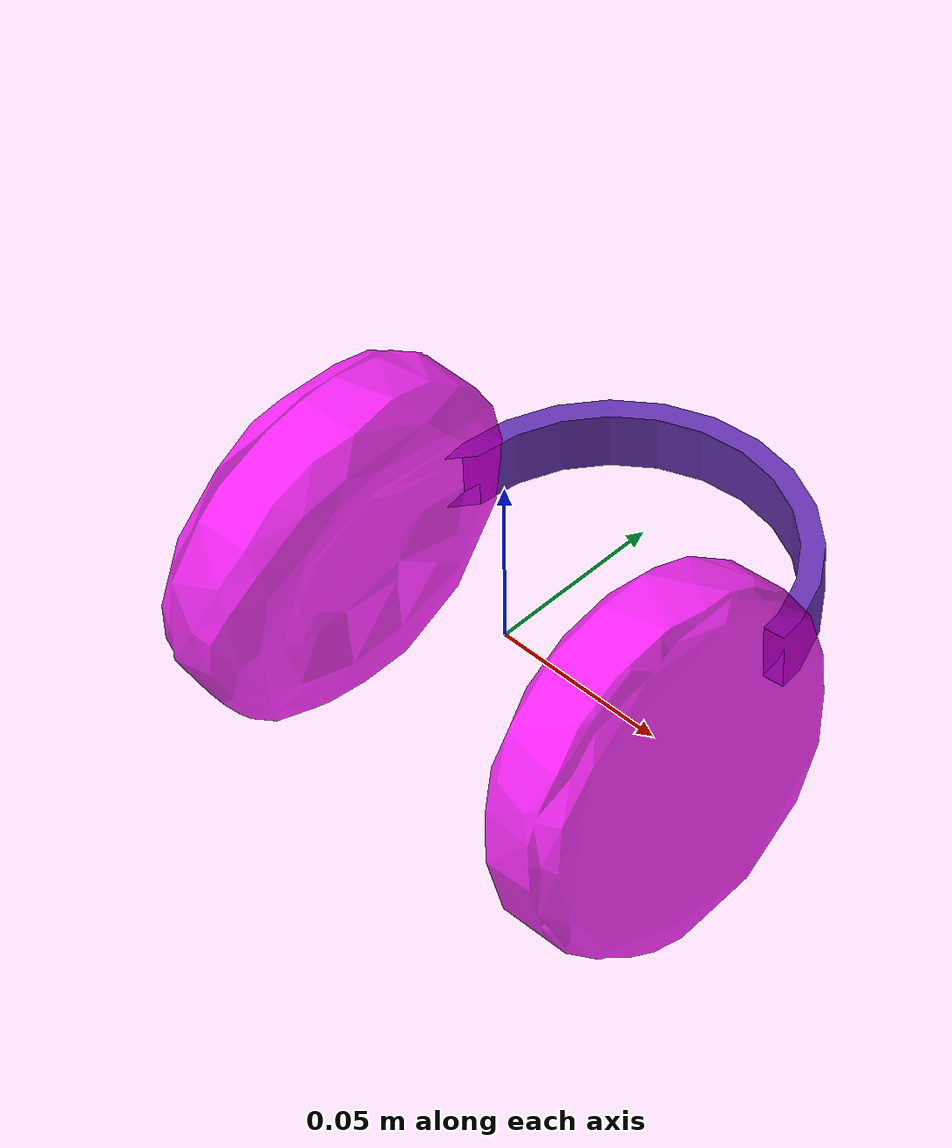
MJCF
<?xml version="1.0" encoding="utf-8"?>
<mujoco model="top_watertight_tiny">

  <default>

    <default group="2" type="mesh" contype="0" conaffinity="0">

      <geom group="2" type="mesh" contype="0" conaffinity="0"/>

    </default>

    <default group="3" type="mesh">

      <geom group="3" type="mesh"/>

    </default>

  </default>

  <asset>

    <mesh file="top_watertight_tiny.obj"/>

    <mesh file="top_watertight_tiny_collision_0.obj"/>

    <mesh file="top_watertight_tiny_collision_1.obj"/>

    <mesh file="top_watertight_tiny_collision_2.obj"/>

    <mesh file="top_watertight_tiny_collision_3.obj"/>

    <mesh file="top_watertight_tiny_collision_4.obj"/>

    <mesh file="top_watertight_tiny_collision_5.obj"/>

    <mesh file="top_watertight_tiny_collision_6.obj"/>

    <mesh file="top_watertight_tiny_collision_7.obj"/>

    <mesh file="top_watertight_tiny_collision_8.obj"/>

    <mesh file="top_watertight_tiny_collision_9.obj"/>

    <mesh file="top_watertight_tiny_collision_10.obj"/>

    <mesh file="top_watertight_tiny_collision_11.obj"/>

    <mesh file="top_watertight_tiny_collision_12.obj"/>

    <mesh file="top_watertight_tiny_collision_13.obj"/>

    <mesh file="top_watertight_tiny_collision_14.obj"/>

    <mesh file="top_watertight_tiny_collision_15.obj"/>

    <mesh file="top_watertight_tiny_collision_16.obj"/>

    <mesh file="top_watertight_tiny_collision_17.obj"/>

    <mesh file="top_watertight_tiny_collision_18.obj"/>

    <mesh file="top_watertight_tiny_collision_19.obj"/>

    <mesh file="top_watertight_tiny_collision_20.obj"/>

    <mesh file="top_watertight_tiny_collision_21.obj"/>

    <mesh file="top_watertight_tiny_collision_22.obj"/>

    <mesh file="top_watertight_tiny_collision_23.obj"/>

    <mesh file="top_watertight_tiny_collision_24.obj"/>

    <mesh file="top_watertight_tiny_collision_25.obj"/>

    <mesh file="top_watertight_tiny_collision_26.obj"/>

    <mesh file="top_watertight_tiny_collision_27.obj"/>

    <mesh file="top_watertight_tiny_collision_28.obj"/>

    <mesh file="top_watertight_tiny_collision_29.obj"/>

    <mesh file="top_watertight_tiny_collision_30.obj"/>

    <mesh file="top_watertight_tiny_collision_31.obj"/>

    <mesh file="top_watertight_tiny_collision_32.obj"/>

    <mesh file="top_watertight_tiny_collision_33.obj"/>

    <mesh file="top_watertight_tiny_collision_34.obj"/>

    <mesh file="top_watertight_tiny_collision_35.obj"/>

    <mesh file="top_watertight_tiny_collision_36.obj"/>

    <mesh file="top_watertight_tiny_collision_37.obj"/>

    <mesh file="top_watertight_tiny_collision_38.obj"/>

    <mesh file="top_watertight_tiny_collision_39.obj"/>

    <mesh file="top_watertight_tiny_collision_40.obj"/>

    <mesh file="top_watertight_tiny_collision_41.obj"/>

    <mesh file="top_watertight_tiny_collision_42.obj"/>

    <mesh file="top_watertight_tiny_collision_43.obj"/>

    <mesh file="top_watertight_tiny_collision_44.obj"/>

    <mesh file="top_watertight_tiny_collision_45.obj"/>

    <mesh file="top_watertight_tiny_collision_46.obj"/>

    <mesh file="top_watertight_tiny_collision_47.obj"/>

    <mesh file="top_watertight_tiny_collision_48.obj"/>

    <mesh file="bottom_watertight_tiny.obj"/>
    <mesh file="bottom_watertight_tiny_collision_0.obj"/>
    <mesh file="bottom_watertight_tiny_collision_1.obj"/>
    <mesh file="bottom_watertight_tiny_collision_2.obj"/>
    <mesh file="bottom_watertight_tiny_collision_3.obj"/>
    <mesh file="bottom_watertight_tiny_collision_4.obj"/>
    <mesh file="bottom_watertight_tiny_collision_5.obj"/>
    <mesh file="bottom_watertight_tiny_collision_6.obj"/>
    <mesh file="bottom_watertight_tiny_collision_7.obj"/>
    <mesh file="bottom_watertight_tiny_collision_8.obj"/>
    <mesh file="bottom_watertight_tiny_collision_9.obj"/>
    <mesh file="bottom_watertight_tiny_collision_10.obj"/>
    <mesh file="bottom_watertight_tiny_collision_11.obj"/>
    <mesh file="bottom_watertight_tiny_collision_12.obj"/>
    <mesh file="bottom_watertight_tiny_collision_13.obj"/>
    <mesh file="bottom_watertight_tiny_collision_14.obj"/>
    <mesh file="bottom_watertight_tiny_collision_15.obj"/>
    <mesh file="bottom_watertight_tiny_collision_16.obj"/>
    <mesh file="bottom_watertight_tiny_collision_17.obj"/>
    <mesh file="bottom_watertight_tiny_collision_18.obj"/>
    <mesh file="bottom_watertight_tiny_collision_19.obj"/>
    <mesh file="bottom_watertight_tiny_collision_20.obj"/>
    <mesh file="bottom_watertight_tiny_collision_21.obj"/>
    <mesh file="bottom_watertight_tiny_collision_22.obj"/>
    <mesh file="bottom_watertight_tiny_collision_23.obj"/>
    <mesh file="bottom_watertight_tiny_collision_24.obj"/>
    <mesh file="bottom_watertight_tiny_collision_25.obj"/>
    <mesh file="bottom_watertight_tiny_collision_26.obj"/>
    <mesh file="bottom_watertight_tiny_collision_27.obj"/>
    <mesh file="bottom_watertight_tiny_collision_28.obj"/>
    <mesh file="bottom_watertight_tiny_collision_29.obj"/>
    <mesh file="bottom_watertight_tiny_collision_30.obj"/>
    <mesh file="bottom_watertight_tiny_collision_31.obj"/>
    <mesh file="bottom_watertight_tiny_collision_32.obj"/>
    <mesh file="bottom_watertight_tiny_collision_33.obj"/>
    <mesh file="bottom_watertight_tiny_collision_34.obj"/>
    <mesh file="bottom_watertight_tiny_collision_35.obj"/>
    <mesh file="bottom_watertight_tiny_collision_36.obj"/>
    <mesh file="bottom_watertight_tiny_collision_37.obj"/>
    <mesh file="bottom_watertight_tiny_collision_38.obj"/>
    <mesh file="bottom_watertight_tiny_collision_39.obj"/>
    <mesh file="bottom_watertight_tiny_collision_40.obj"/>
    <mesh file="bottom_watertight_tiny_collision_41.obj"/>
    <mesh file="bottom_watertight_tiny_collision_42.obj"/>
    <mesh file="bottom_watertight_tiny_collision_43.obj"/>
    <mesh file="bottom_watertight_tiny_collision_44.obj"/>
    <mesh file="bottom_watertight_tiny_collision_45.obj"/>
    <mesh file="bottom_watertight_tiny_collision_46.obj"/>
    <mesh file="bottom_watertight_tiny_collision_47.obj"/>
    <mesh file="bottom_watertight_tiny_collision_48.obj"/>
    <mesh file="bottom_watertight_tiny_collision_49.obj"/>
    <mesh file="bottom_watertight_tiny_collision_50.obj"/>
    <mesh file="bottom_watertight_tiny_collision_51.obj"/>
    <mesh file="bottom_watertight_tiny_collision_52.obj"/>
    <mesh file="bottom_watertight_tiny_collision_53.obj"/>
    <mesh file="bottom_watertight_tiny_collision_54.obj"/>
    <mesh file="bottom_watertight_tiny_collision_55.obj"/>
    <mesh file="bottom_watertight_tiny_collision_56.obj"/>
    <mesh file="bottom_watertight_tiny_collision_57.obj"/>
    <mesh file="bottom_watertight_tiny_collision_58.obj"/>
    <mesh file="bottom_watertight_tiny_collision_59.obj"/>
    <mesh file="bottom_watertight_tiny_collision_60.obj"/>
    <mesh file="bottom_watertight_tiny_collision_61.obj"/>
    <mesh file="bottom_watertight_tiny_collision_62.obj"/>
    <mesh file="bottom_watertight_tiny_collision_63.obj"/>
    <mesh file="bottom_watertight_tiny_collision_64.obj"/>
    <mesh file="bottom_watertight_tiny_collision_65.obj"/>
    <mesh file="bottom_watertight_tiny_collision_66.obj"/>
    <mesh file="bottom_watertight_tiny_collision_67.obj"/>
    <mesh file="bottom_watertight_tiny_collision_68.obj"/>
    <mesh file="bottom_watertight_tiny_collision_69.obj"/>
    <mesh file="bottom_watertight_tiny_collision_70.obj"/>
    <mesh file="bottom_watertight_tiny_collision_71.obj"/>
    <mesh file="bottom_watertight_tiny_collision_72.obj"/>
    <mesh file="bottom_watertight_tiny_collision_73.obj"/>
    <mesh file="bottom_watertight_tiny_collision_74.obj"/>
    <mesh file="bottom_watertight_tiny_collision_75.obj"/>
    <mesh file="bottom_watertight_tiny_collision_76.obj"/>
    <mesh file="bottom_watertight_tiny_collision_77.obj"/>
    <mesh file="bottom_watertight_tiny_collision_78.obj"/>
    <mesh file="bottom_watertight_tiny_collision_79.obj"/>
    <mesh file="bottom_watertight_tiny_collision_80.obj"/>
    <mesh file="bottom_watertight_tiny_collision_81.obj"/>
    <mesh file="bottom_watertight_tiny_collision_82.obj"/>
    <mesh file="bottom_watertight_tiny_collision_83.obj"/>
    <mesh file="bottom_watertight_tiny_collision_84.obj"/>
    <mesh file="bottom_watertight_tiny_collision_85.obj"/>
    <mesh file="bottom_watertight_tiny_collision_86.obj"/>
    <mesh file="bottom_watertight_tiny_collision_87.obj"/>
    <mesh file="bottom_watertight_tiny_collision_88.obj"/>
    <mesh file="bottom_watertight_tiny_collision_89.obj"/>
    <mesh file="bottom_watertight_tiny_collision_90.obj"/>
    <mesh file="bottom_watertight_tiny_collision_91.obj"/>
    <mesh file="bottom_watertight_tiny_collision_92.obj"/>
    <mesh file="bottom_watertight_tiny_collision_93.obj"/>
    <mesh file="bottom_watertight_tiny_collision_94.obj"/>
    <mesh file="bottom_watertight_tiny_collision_95.obj"/>
    <mesh file="bottom_watertight_tiny_collision_96.obj"/>
    <mesh file="bottom_watertight_tiny_collision_97.obj"/>
    <mesh file="bottom_watertight_tiny_collision_98.obj"/>
    <mesh file="bottom_watertight_tiny_collision_99.obj"/>
    <mesh file="bottom_watertight_tiny_collision_100.obj"/>
    <mesh file="bottom_watertight_tiny_collision_101.obj"/>
    <mesh file="bottom_watertight_tiny_collision_102.obj"/>
    <mesh file="bottom_watertight_tiny_collision_103.obj"/>
    <mesh file="bottom_watertight_tiny_collision_104.obj"/>
    <mesh file="bottom_watertight_tiny_collision_105.obj"/>
    <mesh file="bottom_watertight_tiny_collision_106.obj"/>
    <mesh file="bottom_watertight_tiny_collision_107.obj"/>
    <mesh file="bottom_watertight_tiny_collision_108.obj"/>
    <mesh file="bottom_watertight_tiny_collision_109.obj"/>
    <mesh file="bottom_watertight_tiny_collision_110.obj"/>
    <mesh file="bottom_watertight_tiny_collision_111.obj"/>
    <mesh file="bottom_watertight_tiny_collision_112.obj"/>
    <mesh file="bottom_watertight_tiny_collision_113.obj"/>
    <mesh file="bottom_watertight_tiny_collision_114.obj"/>
    <mesh file="bottom_watertight_tiny_collision_115.obj"/>
    <mesh file="bottom_watertight_tiny_collision_116.obj"/>
    <mesh file="bottom_watertight_tiny_collision_117.obj"/>
    <mesh file="bottom_watertight_tiny_collision_118.obj"/>
    <mesh file="bottom_watertight_tiny_collision_119.obj"/>
    <mesh file="bottom_watertight_tiny_collision_120.obj"/>
    <mesh file="bottom_watertight_tiny_collision_121.obj"/>
    <mesh file="bottom_watertight_tiny_collision_122.obj"/>
    <mesh file="bottom_watertight_tiny_collision_123.obj"/>
    <mesh file="bottom_watertight_tiny_collision_124.obj"/>
    <mesh file="bottom_watertight_tiny_collision_125.obj"/>
    <mesh file="bottom_watertight_tiny_collision_126.obj"/>
    <mesh file="bottom_watertight_tiny_collision_127.obj"/>
    <mesh file="bottom_watertight_tiny_collision_128.obj"/>
    <mesh file="bottom_watertight_tiny_collision_129.obj"/>
    <mesh file="bottom_watertight_tiny_collision_130.obj"/>
    <mesh file="bottom_watertight_tiny_collision_131.obj"/>
    <mesh file="bottom_watertight_tiny_collision_132.obj"/>
    <mesh file="bottom_watertight_tiny_collision_133.obj"/>
    <mesh file="bottom_watertight_tiny_collision_134.obj"/>
    <mesh file="bottom_watertight_tiny_collision_135.obj"/>
  </asset>

  <worldbody>

    <body name="top_watertight_tiny">

      <freejoint/>

      <geom mesh="top_watertight_tiny" group="2" type="mesh" rgba="0.4 0.2 0.7 1" contype="0" conaffinity="0" solimp="0.90 0.95 0.001" solref="0.02 1.0" density="100" friction="0.95 0.4 0.3"/>

      <geom mesh="top_watertight_tiny_collision_0" rgba="0.054766574409390034 0.8257619859867841 0.5234326569713394 1" group="3" type="mesh" solimp="0.90 0.95 0.001" solref="0.02 1.0" density="100" friction="0.95 0.4 0.3"/>

      <geom mesh="top_watertight_tiny_collision_1" rgba="0.7978769431043116 0.49282189153257494 0.7981049565845398 1" group="3" type="mesh" solimp="0.90 0.95 0.001" solref="0.02 1.0" density="100" friction="0.95 0.4 0.3"/>

      <geom mesh="top_watertight_tiny_collision_2" rgba="0.5483760204334385 0.033421610627225706 0.10788000055123403 1" group="3" type="mesh" solimp="0.90 0.95 0.001" solref="0.02 1.0" density="100" friction="0.95 0.4 0.3"/>

      <geom mesh="top_watertight_tiny_collision_3" rgba="0.6610493731896853 0.26912904520543246 0.7993828149276015 1" group="3" type="mesh" solimp="0.90 0.95 0.001" solref="0.02 1.0" density="100" friction="0.95 0.4 0.3"/>

      <geom mesh="top_watertight_tiny_collision_4" rgba="0.41500374323461386 0.04771593684570952 0.29880750252037314 1" group="3" type="mesh" solimp="0.90 0.95 0.001" solref="0.02 1.0" density="100" friction="0.95 0.4 0.3"/>

      <geom mesh="top_watertight_tiny_collision_5" rgba="0.6511042234329314 0.623183959921033 0.8190681784601539 1" group="3" type="mesh" solimp="0.90 0.95 0.001" solref="0.02 1.0" density="100" friction="0.95 0.4 0.3"/>

      <geom mesh="top_watertight_tiny_collision_6" rgba="0.7758049502082145 0.6837393850547318 0.8547439775753102 1" group="3" type="mesh" solimp="0.90 0.95 0.001" solref="0.02 1.0" density="100" friction="0.95 0.4 0.3"/>

      <geom mesh="top_watertight_tiny_collision_7" rgba="0.14871852054253398 0.5525202557711464 0.09366229889952016 1" group="3" type="mesh" solimp="0.90 0.95 0.001" solref="0.02 1.0" density="100" friction="0.95 0.4 0.3"/>

      <geom mesh="top_watertight_tiny_collision_8" rgba="0.14754766916585293 0.3219304931507868 0.5908382398647947 1" group="3" type="mesh" solimp="0.90 0.95 0.001" solref="0.02 1.0" density="100" friction="0.95 0.4 0.3"/>

      <geom mesh="top_watertight_tiny_collision_9" rgba="0.1797073374006296 0.10595675739617005 0.7653879463592228 1" group="3" type="mesh" solimp="0.90 0.95 0.001" solref="0.02 1.0" density="100" friction="0.95 0.4 0.3"/>

      <geom mesh="top_watertight_tiny_collision_10" rgba="0.11788538395340298 0.06767147026051523 0.14754316310340265 1" group="3" type="mesh" solimp="0.90 0.95 0.001" solref="0.02 1.0" density="100" friction="0.95 0.4 0.3"/>

      <geom mesh="top_watertight_tiny_collision_11" rgba="0.33838310611199196 0.4552984442786061 0.5609345152001594 1" group="3" type="mesh" solimp="0.90 0.95 0.001" solref="0.02 1.0" density="100" friction="0.95 0.4 0.3"/>

      <geom mesh="top_watertight_tiny_collision_12" rgba="0.9585916384132817 0.3609305994511922 0.18433348999372 1" group="3" type="mesh" solimp="0.90 0.95 0.001" solref="0.02 1.0" density="100" friction="0.95 0.4 0.3"/>

      <geom mesh="top_watertight_tiny_collision_13" rgba="0.5576520100576005 0.7031335425189431 0.740604036037952 1" group="3" type="mesh" solimp="0.90 0.95 0.001" solref="0.02 1.0" density="100" friction="0.95 0.4 0.3"/>

      <geom mesh="top_watertight_tiny_collision_14" rgba="0.23380412248599736 0.5306320062050417 0.12881265691096055 1" group="3" type="mesh" solimp="0.90 0.95 0.001" solref="0.02 1.0" density="100" friction="0.95 0.4 0.3"/>

      <geom mesh="top_watertight_tiny_collision_15" rgba="0.5468047717012718 0.08708672554000108 0.25306766199581154 1" group="3" type="mesh" solimp="0.90 0.95 0.001" solref="0.02 1.0" density="100" friction="0.95 0.4 0.3"/>

      <geom mesh="top_watertight_tiny_collision_16" rgba="0.5491300555036623 0.6527190855319797 0.37963797334792915 1" group="3" type="mesh" solimp="0.90 0.95 0.001" solref="0.02 1.0" density="100" friction="0.95 0.4 0.3"/>

      <geom mesh="top_watertight_tiny_collision_17" rgba="0.7677234626715027 0.7304611380484628 0.3271499260068902 1" group="3" type="mesh" solimp="0.90 0.95 0.001" solref="0.02 1.0" density="100" friction="0.95 0.4 0.3"/>

      <geom mesh="top_watertight_tiny_collision_18" rgba="0.4503029812727778 0.7604409343890279 0.41938507601764763 1" group="3" type="mesh" solimp="0.90 0.95 0.001" solref="0.02 1.0" density="100" friction="0.95 0.4 0.3"/>

      <geom mesh="top_watertight_tiny_collision_19" rgba="0.28049380166474347 0.3873249898427341 0.923140864763082 1" group="3" type="mesh" solimp="0.90 0.95 0.001" solref="0.02 1.0" density="100" friction="0.95 0.4 0.3"/>

      <geom mesh="top_watertight_tiny_collision_20" rgba="0.5623394290126402 0.4546469842979973 0.17293232511643797 1" group="3" type="mesh" solimp="0.90 0.95 0.001" solref="0.02 1.0" density="100" friction="0.95 0.4 0.3"/>

      <geom mesh="top_watertight_tiny_collision_21" rgba="0.8286284342250301 0.6182275033823259 0.4543263116620875 1" group="3" type="mesh" solimp="0.90 0.95 0.001" solref="0.02 1.0" density="100" friction="0.95 0.4 0.3"/>

      <geom mesh="top_watertight_tiny_collision_22" rgba="0.5892584276974225 0.19985754960617752 0.8413173148658565 1" group="3" type="mesh" solimp="0.90 0.95 0.001" solref="0.02 1.0" density="100" friction="0.95 0.4 0.3"/>

      <geom mesh="top_watertight_tiny_collision_23" rgba="0.05486193318001398 0.7435129012244571 0.8422754919208074 1" group="3" type="mesh" solimp="0.90 0.95 0.001" solref="0.02 1.0" density="100" friction="0.95 0.4 0.3"/>

      <geom mesh="top_watertight_tiny_collision_24" rgba="0.669550070729594 0.7228584932278661 0.3284181045097494 1" group="3" type="mesh" solimp="0.90 0.95 0.001" solref="0.02 1.0" density="100" friction="0.95 0.4 0.3"/>

      <geom mesh="top_watertight_tiny_collision_25" rgba="0.20798412784756837 0.41411066328777246 0.6259495567916469 1" group="3" type="mesh" solimp="0.90 0.95 0.001" solref="0.02 1.0" density="100" friction="0.95 0.4 0.3"/>

      <geom mesh="top_watertight_tiny_collision_26" rgba="0.4663647216197224 0.14338082401105323 0.9057203173151067 1" group="3" type="mesh" solimp="0.90 0.95 0.001" solref="0.02 1.0" density="100" friction="0.95 0.4 0.3"/>

      <geom mesh="top_watertight_tiny_collision_27" rgba="0.2804452664236955 0.780701018373259 0.9950050771856404 1" group="3" type="mesh" solimp="0.90 0.95 0.001" solref="0.02 1.0" density="100" friction="0.95 0.4 0.3"/>

      <geom mesh="top_watertight_tiny_collision_28" rgba="0.9411776949249658 0.5070683743964342 0.307292056069115 1" group="3" type="mesh" solimp="0.90 0.95 0.001" solref="0.02 1.0" density="100" friction="0.95 0.4 0.3"/>

      <geom mesh="top_watertight_tiny_collision_29" rgba="0.03802084657765337 0.2921487776439329 0.11154980401103609 1" group="3" type="mesh" solimp="0.90 0.95 0.001" solref="0.02 1.0" density="100" friction="0.95 0.4 0.3"/>

      <geom mesh="top_watertight_tiny_collision_30" rgba="0.2571192946027683 0.6420962064801935 0.21568170356695315 1" group="3" type="mesh" solimp="0.90 0.95 0.001" solref="0.02 1.0" density="100" friction="0.95 0.4 0.3"/>

      <geom mesh="top_watertight_tiny_collision_31" rgba="0.5413519303750494 0.7546566535049081 0.2420988527997604 1" group="3" type="mesh" solimp="0.90 0.95 0.001" solref="0.02 1.0" density="100" friction="0.95 0.4 0.3"/>

      <geom mesh="top_watertight_tiny_collision_32" rgba="0.5908259530017747 0.3314752746613826 0.8425418262340508 1" group="3" type="mesh" solimp="0.90 0.95 0.001" solref="0.02 1.0" density="100" friction="0.95 0.4 0.3"/>

      <geom mesh="top_watertight_tiny_collision_33" rgba="0.6762617927528107 0.930611152456162 0.3461668792379706 1" group="3" type="mesh" solimp="0.90 0.95 0.001" solref="0.02 1.0" density="100" friction="0.95 0.4 0.3"/>

      <geom mesh="top_watertight_tiny_collision_34" rgba="0.8812970270589525 0.4037957883597235 0.8553874653617136 1" group="3" type="mesh" solimp="0.90 0.95 0.001" solref="0.02 1.0" density="100" friction="0.95 0.4 0.3"/>

      <geom mesh="top_watertight_tiny_collision_35" rgba="0.36912888928042675 0.4251878725227828 0.40444383906355996 1" group="3" type="mesh" solimp="0.90 0.95 0.001" solref="0.02 1.0" density="100" friction="0.95 0.4 0.3"/>

      <geom mesh="top_watertight_tiny_collision_36" rgba="0.15604037312399588 0.0787973412876588 0.5975490258511297 1" group="3" type="mesh" solimp="0.90 0.95 0.001" solref="0.02 1.0" density="100" friction="0.95 0.4 0.3"/>

      <geom mesh="top_watertight_tiny_collision_37" rgba="0.12764292383803388 0.5254256655203879 0.17252788996726143 1" group="3" type="mesh" solimp="0.90 0.95 0.001" solref="0.02 1.0" density="100" friction="0.95 0.4 0.3"/>

      <geom mesh="top_watertight_tiny_collision_38" rgba="0.4633717223539159 0.4334789290632529 0.9822731510356043 1" group="3" type="mesh" solimp="0.90 0.95 0.001" solref="0.02 1.0" density="100" friction="0.95 0.4 0.3"/>

      <geom mesh="top_watertight_tiny_collision_39" rgba="0.6395733890238732 0.9646504749633156 0.771997697302216 1" group="3" type="mesh" solimp="0.90 0.95 0.001" solref="0.02 1.0" density="100" friction="0.95 0.4 0.3"/>

      <geom mesh="top_watertight_tiny_collision_40" rgba="0.8607552614530602 0.43830241057666486 0.39872297777397203 1" group="3" type="mesh" solimp="0.90 0.95 0.001" solref="0.02 1.0" density="100" friction="0.95 0.4 0.3"/>

      <geom mesh="top_watertight_tiny_collision_41" rgba="0.1723773047827606 0.19592694314138226 0.6453344920793619 1" group="3" type="mesh" solimp="0.90 0.95 0.001" solref="0.02 1.0" density="100" friction="0.95 0.4 0.3"/>

      <geom mesh="top_watertight_tiny_collision_42" rgba="0.6473429029090425 0.16704357107014123 0.7658071486849389 1" group="3" type="mesh" solimp="0.90 0.95 0.001" solref="0.02 1.0" density="100" friction="0.95 0.4 0.3"/>

      <geom mesh="top_watertight_tiny_collision_43" rgba="0.716802580913184 0.04315659707036312 0.033241066932502394 1" group="3" type="mesh" solimp="0.90 0.95 0.001" solref="0.02 1.0" density="100" friction="0.95 0.4 0.3"/>

      <geom mesh="top_watertight_tiny_collision_44" rgba="0.673023396624791 0.17330916854073408 0.7689490055662221 1" group="3" type="mesh" solimp="0.90 0.95 0.001" solref="0.02 1.0" density="100" friction="0.95 0.4 0.3"/>

      <geom mesh="top_watertight_tiny_collision_45" rgba="0.5982475624635203 0.9466662587102092 0.7954086306227927 1" group="3" type="mesh" solimp="0.90 0.95 0.001" solref="0.02 1.0" density="100" friction="0.95 0.4 0.3"/>

      <geom mesh="top_watertight_tiny_collision_46" rgba="0.9722848470640117 0.025905716488464625 0.9787787884326711 1" group="3" type="mesh" solimp="0.90 0.95 0.001" solref="0.02 1.0" density="100" friction="0.95 0.4 0.3"/>

      <geom mesh="top_watertight_tiny_collision_47" rgba="0.22909829023532724 0.10800953480732423 0.3274292580093425 1" group="3" type="mesh" solimp="0.90 0.95 0.001" solref="0.02 1.0" density="100" friction="0.95 0.4 0.3"/>

      <geom mesh="top_watertight_tiny_collision_48" rgba="0.5919222923530667 0.17181664271053732 0.4585360725730083 1" group="3" type="mesh" solimp="0.90 0.95 0.001" solref="0.02 1.0" density="100" friction="0.95 0.4 0.3"/>

      <body name="bottom_watertight_tiny">

        <geom mesh="bottom_watertight_tiny" group="2" type="mesh" rgba="1 0 1 0.8" contype="0" conaffinity="0" solimp="0.90 0.95 0.001" solref="0.02 1.0" density="100" friction="0.95 0.4 0.3"/>

        <geom mesh="bottom_watertight_tiny_collision_0" rgba="0.343983961661921 0.8265252202562995 0.13284787692748856 1" group="3" type="mesh" solimp="0.90 0.95 0.001" solref="0.02 1.0" density="100" friction="0.95 0.4 0.3"/>

        <geom mesh="bottom_watertight_tiny_collision_1" rgba="0.3194055916005605 0.8057906767615574 0.8803331639467502 1" group="3" type="mesh" solimp="0.90 0.95 0.001" solref="0.02 1.0" density="100" friction="0.95 0.4 0.3"/>

        <geom mesh="bottom_watertight_tiny_collision_2" rgba="0.7855915020937909 0.9714109539470092 0.8338949052306774 1" group="3" type="mesh" solimp="0.90 0.95 0.001" solref="0.02 1.0" density="100" friction="0.95 0.4 0.3"/>

        <geom mesh="bottom_watertight_tiny_collision_3" rgba="0.8930281943021798 0.05415432223553929 0.03153233702283886 1" group="3" type="mesh" solimp="0.90 0.95 0.001" solref="0.02 1.0" density="100" friction="0.95 0.4 0.3"/>

        <geom mesh="bottom_watertight_tiny_collision_4" rgba="0.08708408160782599 0.2864046861939905 0.2717874603109256 1" group="3" type="mesh" solimp="0.90 0.95 0.001" solref="0.02 1.0" density="100" friction="0.95 0.4 0.3"/>

        <geom mesh="bottom_watertight_tiny_collision_5" rgba="0.7207351785391303 0.6435978758937029 0.4643230739372236 1" group="3" type="mesh" solimp="0.90 0.95 0.001" solref="0.02 1.0" density="100" friction="0.95 0.4 0.3"/>

        <geom mesh="bottom_watertight_tiny_collision_6" rgba="0.3750963646015647 0.8725637275187305 0.7862124608952091 1" group="3" type="mesh" solimp="0.90 0.95 0.001" solref="0.02 1.0" density="100" friction="0.95 0.4 0.3"/>

        <geom mesh="bottom_watertight_tiny_collision_7" rgba="0.2613527370169043 0.9032502995505594 0.3412458997021669 1" group="3" type="mesh" solimp="0.90 0.95 0.001" solref="0.02 1.0" density="100" friction="0.95 0.4 0.3"/>

        <geom mesh="bottom_watertight_tiny_collision_8" rgba="0.35013783934831 0.6737606481972477 0.6890655871196877 1" group="3" type="mesh" solimp="0.90 0.95 0.001" solref="0.02 1.0" density="100" friction="0.95 0.4 0.3"/>

        <geom mesh="bottom_watertight_tiny_collision_9" rgba="0.04668471114255135 0.7795732560623482 0.7597667862949882 1" group="3" type="mesh" solimp="0.90 0.95 0.001" solref="0.02 1.0" density="100" friction="0.95 0.4 0.3"/>

        <geom mesh="bottom_watertight_tiny_collision_10" rgba="0.7688320833598374 0.329861286168055 0.7407011338129389 1" group="3" type="mesh" solimp="0.90 0.95 0.001" solref="0.02 1.0" density="100" friction="0.95 0.4 0.3"/>

        <geom mesh="bottom_watertight_tiny_collision_11" rgba="0.21427164311836255 0.13566087382938985 0.04009118134443135 1" group="3" type="mesh" solimp="0.90 0.95 0.001" solref="0.02 1.0" density="100" friction="0.95 0.4 0.3"/>

        <geom mesh="bottom_watertight_tiny_collision_12" rgba="0.9636389173730365 0.5011324578945223 0.6240546535725233 1" group="3" type="mesh" solimp="0.90 0.95 0.001" solref="0.02 1.0" density="100" friction="0.95 0.4 0.3"/>

        <geom mesh="bottom_watertight_tiny_collision_13" rgba="0.08919720477961357 0.9080392404710729 0.28706429121932875 1" group="3" type="mesh" solimp="0.90 0.95 0.001" solref="0.02 1.0" density="100" friction="0.95 0.4 0.3"/>

        <geom mesh="bottom_watertight_tiny_collision_14" rgba="0.03014970687095908 0.24169888326492206 0.3912231486107558 1" group="3" type="mesh" solimp="0.90 0.95 0.001" solref="0.02 1.0" density="100" friction="0.95 0.4 0.3"/>

        <geom mesh="bottom_watertight_tiny_collision_15" rgba="0.8986278561609606 0.37876300768715876 0.11162276914907787 1" group="3" type="mesh" solimp="0.90 0.95 0.001" solref="0.02 1.0" density="100" friction="0.95 0.4 0.3"/>

        <geom mesh="bottom_watertight_tiny_collision_16" rgba="0.15689793007886377 0.5676848878055039 0.3238288627020136 1" group="3" type="mesh" solimp="0.90 0.95 0.001" solref="0.02 1.0" density="100" friction="0.95 0.4 0.3"/>

        <geom mesh="bottom_watertight_tiny_collision_17" rgba="0.9685830070657376 0.0628198187548119 0.9488883277485496 1" group="3" type="mesh" solimp="0.90 0.95 0.001" solref="0.02 1.0" density="100" friction="0.95 0.4 0.3"/>

        <geom mesh="bottom_watertight_tiny_collision_18" rgba="0.5912275863034104 0.2908098157292448 0.26868654033489525 1" group="3" type="mesh" solimp="0.90 0.95 0.001" solref="0.02 1.0" density="100" friction="0.95 0.4 0.3"/>

        <geom mesh="bottom_watertight_tiny_collision_19" rgba="0.7176323415879392 0.557154299448974 0.7406940553999988 1" group="3" type="mesh" solimp="0.90 0.95 0.001" solref="0.02 1.0" density="100" friction="0.95 0.4 0.3"/>

        <geom mesh="bottom_watertight_tiny_collision_20" rgba="0.9841576436874294 0.4332284643496388 0.15638359361309306 1" group="3" type="mesh" solimp="0.90 0.95 0.001" solref="0.02 1.0" density="100" friction="0.95 0.4 0.3"/>

        <geom mesh="bottom_watertight_tiny_collision_21" rgba="0.6180613364201043 0.8198999623044012 0.2385574639140352 1" group="3" type="mesh" solimp="0.90 0.95 0.001" solref="0.02 1.0" density="100" friction="0.95 0.4 0.3"/>

        <geom mesh="bottom_watertight_tiny_collision_22" rgba="0.5967332002963099 0.891926396280934 0.6228813851339599 1" group="3" type="mesh" solimp="0.90 0.95 0.001" solref="0.02 1.0" density="100" friction="0.95 0.4 0.3"/>

        <geom mesh="bottom_watertight_tiny_collision_23" rgba="0.19547715709992475 0.7591739261729155 0.08604754322445529 1" group="3" type="mesh" solimp="0.90 0.95 0.001" solref="0.02 1.0" density="100" friction="0.95 0.4 0.3"/>

        <geom mesh="bottom_watertight_tiny_collision_24" rgba="0.9881510929176015 0.5748738801166149 0.46247548955789075 1" group="3" type="mesh" solimp="0.90 0.95 0.001" solref="0.02 1.0" density="100" friction="0.95 0.4 0.3"/>

        <geom mesh="bottom_watertight_tiny_collision_25" rgba="0.29468966582807155 0.6426619157699964 0.7095125326873261 1" group="3" type="mesh" solimp="0.90 0.95 0.001" solref="0.02 1.0" density="100" friction="0.95 0.4 0.3"/>

        <geom mesh="bottom_watertight_tiny_collision_26" rgba="0.20347465347506988 0.2511761597584564 0.3405812511413626 1" group="3" type="mesh" solimp="0.90 0.95 0.001" solref="0.02 1.0" density="100" friction="0.95 0.4 0.3"/>

        <geom mesh="bottom_watertight_tiny_collision_27" rgba="0.8918875804122384 0.929462734676355 0.4938376579568421 1" group="3" type="mesh" solimp="0.90 0.95 0.001" solref="0.02 1.0" density="100" friction="0.95 0.4 0.3"/>

        <geom mesh="bottom_watertight_tiny_collision_28" rgba="0.38147852034724394 0.6293185856104611 0.7201055217412289 1" group="3" type="mesh" solimp="0.90 0.95 0.001" solref="0.02 1.0" density="100" friction="0.95 0.4 0.3"/>

        <geom mesh="bottom_watertight_tiny_collision_29" rgba="0.7414846510346782 0.17562720039738045 0.48250096685291655 1" group="3" type="mesh" solimp="0.90 0.95 0.001" solref="0.02 1.0" density="100" friction="0.95 0.4 0.3"/>

        <geom mesh="bottom_watertight_tiny_collision_30" rgba="0.037205647956975785 0.10340449655801487 0.6615296692783991 1" group="3" type="mesh" solimp="0.90 0.95 0.001" solref="0.02 1.0" density="100" friction="0.95 0.4 0.3"/>

        <geom mesh="bottom_watertight_tiny_collision_31" rgba="0.9297801146355822 0.46801553846129074 0.2347411326234492 1" group="3" type="mesh" solimp="0.90 0.95 0.001" solref="0.02 1.0" density="100" friction="0.95 0.4 0.3"/>

        <geom mesh="bottom_watertight_tiny_collision_32" rgba="0.7420490912608247 0.09550641539302396 0.7304489483119625 1" group="3" type="mesh" solimp="0.90 0.95 0.001" solref="0.02 1.0" density="100" friction="0.95 0.4 0.3"/>

        <geom mesh="bottom_watertight_tiny_collision_33" rgba="0.9038308333753271 0.9420714528040767 0.844773614726547 1" group="3" type="mesh" solimp="0.90 0.95 0.001" solref="0.02 1.0" density="100" friction="0.95 0.4 0.3"/>

        <geom mesh="bottom_watertight_tiny_collision_34" rgba="0.42024829532081176 0.8448945812810347 0.6831909471245721 1" group="3" type="mesh" solimp="0.90 0.95 0.001" solref="0.02 1.0" density="100" friction="0.95 0.4 0.3"/>

        <geom mesh="bottom_watertight_tiny_collision_35" rgba="0.05427756847877907 0.42814089340868633 0.3926643461886279 1" group="3" type="mesh" solimp="0.90 0.95 0.001" solref="0.02 1.0" density="100" friction="0.95 0.4 0.3"/>

        <geom mesh="bottom_watertight_tiny_collision_36" rgba="0.7471367519218315 0.23319174011938604 0.22045243034629058 1" group="3" type="mesh" solimp="0.90 0.95 0.001" solref="0.02 1.0" density="100" friction="0.95 0.4 0.3"/>

        <geom mesh="bottom_watertight_tiny_collision_37" rgba="0.07522603507721615 0.8707260205058809 0.4994422474077431 1" group="3" type="mesh" solimp="0.90 0.95 0.001" solref="0.02 1.0" density="100" friction="0.95 0.4 0.3"/>

        <geom mesh="bottom_watertight_tiny_collision_38" rgba="0.6172914369171891 0.6508378482415212 0.45172850227155303 1" group="3" type="mesh" solimp="0.90 0.95 0.001" solref="0.02 1.0" density="100" friction="0.95 0.4 0.3"/>

        <geom mesh="bottom_watertight_tiny_collision_39" rgba="0.9185001559655113 0.8516851029942348 0.9420075317591242 1" group="3" type="mesh" solimp="0.90 0.95 0.001" solref="0.02 1.0" density="100" friction="0.95 0.4 0.3"/>

        <geom mesh="bottom_watertight_tiny_collision_40" rgba="0.034863621607103656 0.8782419890039975 0.9127873819220924 1" group="3" type="mesh" solimp="0.90 0.95 0.001" solref="0.02 1.0" density="100" friction="0.95 0.4 0.3"/>

        <geom mesh="bottom_watertight_tiny_collision_41" rgba="0.33120616220464527 0.8323354954987767 0.4498934354065097 1" group="3" type="mesh" solimp="0.90 0.95 0.001" solref="0.02 1.0" density="100" friction="0.95 0.4 0.3"/>

        <geom mesh="bottom_watertight_tiny_collision_42" rgba="0.49000874270299466 0.010144308319176232 0.8788787672628716 1" group="3" type="mesh" solimp="0.90 0.95 0.001" solref="0.02 1.0" density="100" friction="0.95 0.4 0.3"/>

        <geom mesh="bottom_watertight_tiny_collision_43" rgba="0.5752265849391425 0.5585089375048772 0.09215530008360273 1" group="3" type="mesh" solimp="0.90 0.95 0.001" solref="0.02 1.0" density="100" friction="0.95 0.4 0.3"/>

        <geom mesh="bottom_watertight_tiny_collision_44" rgba="0.7019140877193115 0.2298688722353629 0.17683810086558338 1" group="3" type="mesh" solimp="0.90 0.95 0.001" solref="0.02 1.0" density="100" friction="0.95 0.4 0.3"/>

        <geom mesh="bottom_watertight_tiny_collision_45" rgba="0.39298100881531073 0.3431067080501776 0.6496507542508466 1" group="3" type="mesh" solimp="0.90 0.95 0.001" solref="0.02 1.0" density="100" friction="0.95 0.4 0.3"/>

        <geom mesh="bottom_watertight_tiny_collision_46" rgba="0.5715024183196362 0.6397382500797486 0.5403481083438465 1" group="3" type="mesh" solimp="0.90 0.95 0.001" solref="0.02 1.0" density="100" friction="0.95 0.4 0.3"/>

        <geom mesh="bottom_watertight_tiny_collision_47" rgba="0.7305296258952038 0.5351263117981852 0.017336988743503867 1" group="3" type="mesh" solimp="0.90 0.95 0.001" solref="0.02 1.0" density="100" friction="0.95 0.4 0.3"/>

        <geom mesh="bottom_watertight_tiny_collision_48" rgba="0.05459667205951568 0.08834279104849097 0.5093282732739031 1" group="3" type="mesh" solimp="0.90 0.95 0.001" solref="0.02 1.0" density="100" friction="0.95 0.4 0.3"/>

        <geom mesh="bottom_watertight_tiny_collision_49" rgba="0.30103752217655566 0.7980337660127775 0.8251304310997974 1" group="3" type="mesh" solimp="0.90 0.95 0.001" solref="0.02 1.0" density="100" friction="0.95 0.4 0.3"/>

        <geom mesh="bottom_watertight_tiny_collision_50" rgba="0.3607437438385136 0.05134278481681287 0.08998311444777285 1" group="3" type="mesh" solimp="0.90 0.95 0.001" solref="0.02 1.0" density="100" friction="0.95 0.4 0.3"/>

        <geom mesh="bottom_watertight_tiny_collision_51" rgba="0.35423885947232514 0.27247573530469393 0.7289626229888108 1" group="3" type="mesh" solimp="0.90 0.95 0.001" solref="0.02 1.0" density="100" friction="0.95 0.4 0.3"/>

        <geom mesh="bottom_watertight_tiny_collision_52" rgba="0.370055666948351 0.9892515638785715 0.392899317711666 1" group="3" type="mesh" solimp="0.90 0.95 0.001" solref="0.02 1.0" density="100" friction="0.95 0.4 0.3"/>

        <geom mesh="bottom_watertight_tiny_collision_53" rgba="0.4044292570895527 0.47311105830389166 0.1388221328895045 1" group="3" type="mesh" solimp="0.90 0.95 0.001" solref="0.02 1.0" density="100" friction="0.95 0.4 0.3"/>

        <geom mesh="bottom_watertight_tiny_collision_54" rgba="0.09176018267660957 0.09339533799083477 0.4374945914822779 1" group="3" type="mesh" solimp="0.90 0.95 0.001" solref="0.02 1.0" density="100" friction="0.95 0.4 0.3"/>

        <geom mesh="bottom_watertight_tiny_collision_55" rgba="0.5461388532312813 0.016759595186619847 0.7254361092180271 1" group="3" type="mesh" solimp="0.90 0.95 0.001" solref="0.02 1.0" density="100" friction="0.95 0.4 0.3"/>

        <geom mesh="bottom_watertight_tiny_collision_56" rgba="0.1235489290474433 0.9108297872710988 0.45252421127716735 1" group="3" type="mesh" solimp="0.90 0.95 0.001" solref="0.02 1.0" density="100" friction="0.95 0.4 0.3"/>

        <geom mesh="bottom_watertight_tiny_collision_57" rgba="0.26495956018594147 0.3167515735302755 0.811385928390581 1" group="3" type="mesh" solimp="0.90 0.95 0.001" solref="0.02 1.0" density="100" friction="0.95 0.4 0.3"/>

        <geom mesh="bottom_watertight_tiny_collision_58" rgba="0.7341685185789193 0.3850037409557481 0.8095261439489876 1" group="3" type="mesh" solimp="0.90 0.95 0.001" solref="0.02 1.0" density="100" friction="0.95 0.4 0.3"/>

        <geom mesh="bottom_watertight_tiny_collision_59" rgba="0.452623311735038 0.6136775086241901 0.801542387412665 1" group="3" type="mesh" solimp="0.90 0.95 0.001" solref="0.02 1.0" density="100" friction="0.95 0.4 0.3"/>

        <geom mesh="bottom_watertight_tiny_collision_60" rgba="0.4986501059467717 0.021242144926344686 0.47719922416560734 1" group="3" type="mesh" solimp="0.90 0.95 0.001" solref="0.02 1.0" density="100" friction="0.95 0.4 0.3"/>

        <geom mesh="bottom_watertight_tiny_collision_61" rgba="0.131289195871634 0.02084726582356744 0.1890237123558176 1" group="3" type="mesh" solimp="0.90 0.95 0.001" solref="0.02 1.0" density="100" friction="0.95 0.4 0.3"/>

        <geom mesh="bottom_watertight_tiny_collision_62" rgba="0.07764451143493545 0.6218834774228826 0.509910569156977 1" group="3" type="mesh" solimp="0.90 0.95 0.001" solref="0.02 1.0" density="100" friction="0.95 0.4 0.3"/>

        <geom mesh="bottom_watertight_tiny_collision_63" rgba="0.5052857661489365 0.4067009790725342 0.5690731962195783 1" group="3" type="mesh" solimp="0.90 0.95 0.001" solref="0.02 1.0" density="100" friction="0.95 0.4 0.3"/>

        <geom mesh="bottom_watertight_tiny_collision_64" rgba="0.18385737515191836 0.4434461968688467 0.677160788574089 1" group="3" type="mesh" solimp="0.90 0.95 0.001" solref="0.02 1.0" density="100" friction="0.95 0.4 0.3"/>

        <geom mesh="bottom_watertight_tiny_collision_65" rgba="0.15133791833799848 0.9230941027242578 0.10735012138268951 1" group="3" type="mesh" solimp="0.90 0.95 0.001" solref="0.02 1.0" density="100" friction="0.95 0.4 0.3"/>

        <geom mesh="bottom_watertight_tiny_collision_66" rgba="0.5099988959236318 0.07698933820598042 0.0850779869125019 1" group="3" type="mesh" solimp="0.90 0.95 0.001" solref="0.02 1.0" density="100" friction="0.95 0.4 0.3"/>

        <geom mesh="bottom_watertight_tiny_collision_67" rgba="0.167397893186229 0.8218893867466305 0.9545686591057811 1" group="3" type="mesh" solimp="0.90 0.95 0.001" solref="0.02 1.0" density="100" friction="0.95 0.4 0.3"/>

        <geom mesh="bottom_watertight_tiny_collision_68" rgba="0.8069877112675083 0.5945218555556843 0.6346009905650394 1" group="3" type="mesh" solimp="0.90 0.95 0.001" solref="0.02 1.0" density="100" friction="0.95 0.4 0.3"/>

        <geom mesh="bottom_watertight_tiny_collision_69" rgba="0.31376348952320066 0.1300711560650457 0.7654040944051737 1" group="3" type="mesh" solimp="0.90 0.95 0.001" solref="0.02 1.0" density="100" friction="0.95 0.4 0.3"/>

        <geom mesh="bottom_watertight_tiny_collision_70" rgba="0.252749179030194 0.9084643273155428 0.4321187457033001 1" group="3" type="mesh" solimp="0.90 0.95 0.001" solref="0.02 1.0" density="100" friction="0.95 0.4 0.3"/>

        <geom mesh="bottom_watertight_tiny_collision_71" rgba="0.6443258537093467 0.947664783877765 0.6854675973528076 1" group="3" type="mesh" solimp="0.90 0.95 0.001" solref="0.02 1.0" density="100" friction="0.95 0.4 0.3"/>

        <geom mesh="bottom_watertight_tiny_collision_72" rgba="0.8873241535690932 0.9562115097711552 0.9376440791565502 1" group="3" type="mesh" solimp="0.90 0.95 0.001" solref="0.02 1.0" density="100" friction="0.95 0.4 0.3"/>

        <geom mesh="bottom_watertight_tiny_collision_73" rgba="0.8492830563653951 0.21282425983235942 0.45980272035196545 1" group="3" type="mesh" solimp="0.90 0.95 0.001" solref="0.02 1.0" density="100" friction="0.95 0.4 0.3"/>

        <geom mesh="bottom_watertight_tiny_collision_74" rgba="0.6066571561413728 0.62725432484941 0.2973354717655846 1" group="3" type="mesh" solimp="0.90 0.95 0.001" solref="0.02 1.0" density="100" friction="0.95 0.4 0.3"/>

        <geom mesh="bottom_watertight_tiny_collision_75" rgba="0.9141105639467875 0.4404567878436273 0.8534746495232746 1" group="3" type="mesh" solimp="0.90 0.95 0.001" solref="0.02 1.0" density="100" friction="0.95 0.4 0.3"/>

        <geom mesh="bottom_watertight_tiny_collision_76" rgba="0.9719167992671613 0.4972695560742739 0.8234460186802197 1" group="3" type="mesh" solimp="0.90 0.95 0.001" solref="0.02 1.0" density="100" friction="0.95 0.4 0.3"/>

        <geom mesh="bottom_watertight_tiny_collision_77" rgba="0.6928089461263429 0.40925381874516653 0.3895107509980198 1" group="3" type="mesh" solimp="0.90 0.95 0.001" solref="0.02 1.0" density="100" friction="0.95 0.4 0.3"/>

        <geom mesh="bottom_watertight_tiny_collision_78" rgba="0.5554193998854674 0.6098015098208202 0.7165191012465035 1" group="3" type="mesh" solimp="0.90 0.95 0.001" solref="0.02 1.0" density="100" friction="0.95 0.4 0.3"/>

        <geom mesh="bottom_watertight_tiny_collision_79" rgba="0.04649745578972109 0.6192924444221228 0.03448541996185883 1" group="3" type="mesh" solimp="0.90 0.95 0.001" solref="0.02 1.0" density="100" friction="0.95 0.4 0.3"/>

        <geom mesh="bottom_watertight_tiny_collision_80" rgba="0.5067363067447064 0.43091404213856865 0.2944141459135097 1" group="3" type="mesh" solimp="0.90 0.95 0.001" solref="0.02 1.0" density="100" friction="0.95 0.4 0.3"/>

        <geom mesh="bottom_watertight_tiny_collision_81" rgba="0.05373044386657322 0.31160853478220085 0.6704817983799953 1" group="3" type="mesh" solimp="0.90 0.95 0.001" solref="0.02 1.0" density="100" friction="0.95 0.4 0.3"/>

        <geom mesh="bottom_watertight_tiny_collision_82" rgba="0.04311798590876981 0.3404953875303851 0.47649416892334706 1" group="3" type="mesh" solimp="0.90 0.95 0.001" solref="0.02 1.0" density="100" friction="0.95 0.4 0.3"/>

        <geom mesh="bottom_watertight_tiny_collision_83" rgba="0.6326948969439136 0.12942544244269094 0.6520854243172629 1" group="3" type="mesh" solimp="0.90 0.95 0.001" solref="0.02 1.0" density="100" friction="0.95 0.4 0.3"/>

        <geom mesh="bottom_watertight_tiny_collision_84" rgba="0.17132317517340045 0.04931769964823984 0.9899046865843792 1" group="3" type="mesh" solimp="0.90 0.95 0.001" solref="0.02 1.0" density="100" friction="0.95 0.4 0.3"/>

        <geom mesh="bottom_watertight_tiny_collision_85" rgba="0.1549655274567927 0.6967942226159801 0.3333350089326965 1" group="3" type="mesh" solimp="0.90 0.95 0.001" solref="0.02 1.0" density="100" friction="0.95 0.4 0.3"/>

        <geom mesh="bottom_watertight_tiny_collision_86" rgba="0.13471145517938732 0.1020746715655848 0.4260935085994072 1" group="3" type="mesh" solimp="0.90 0.95 0.001" solref="0.02 1.0" density="100" friction="0.95 0.4 0.3"/>

        <geom mesh="bottom_watertight_tiny_collision_87" rgba="0.03046985357123333 0.6933891060188054 0.7455132172539455 1" group="3" type="mesh" solimp="0.90 0.95 0.001" solref="0.02 1.0" density="100" friction="0.95 0.4 0.3"/>

        <geom mesh="bottom_watertight_tiny_collision_88" rgba="0.8381630428225416 0.32636849136945045 0.02127926089858312 1" group="3" type="mesh" solimp="0.90 0.95 0.001" solref="0.02 1.0" density="100" friction="0.95 0.4 0.3"/>

        <geom mesh="bottom_watertight_tiny_collision_89" rgba="0.1752996313613855 0.02735742831406529 0.939836424503685 1" group="3" type="mesh" solimp="0.90 0.95 0.001" solref="0.02 1.0" density="100" friction="0.95 0.4 0.3"/>

        <geom mesh="bottom_watertight_tiny_collision_90" rgba="0.33392152990768853 0.028249497761380082 0.7503062748366564 1" group="3" type="mesh" solimp="0.90 0.95 0.001" solref="0.02 1.0" density="100" friction="0.95 0.4 0.3"/>

        <geom mesh="bottom_watertight_tiny_collision_91" rgba="0.4998629175779946 0.39074904686220135 0.5940266049946968 1" group="3" type="mesh" solimp="0.90 0.95 0.001" solref="0.02 1.0" density="100" friction="0.95 0.4 0.3"/>

        <geom mesh="bottom_watertight_tiny_collision_92" rgba="0.2125725490200705 0.7228324905808494 0.803042290339224 1" group="3" type="mesh" solimp="0.90 0.95 0.001" solref="0.02 1.0" density="100" friction="0.95 0.4 0.3"/>

        <geom mesh="bottom_watertight_tiny_collision_93" rgba="0.7770566745734663 0.8296294703692659 0.20665387500863142 1" group="3" type="mesh" solimp="0.90 0.95 0.001" solref="0.02 1.0" density="100" friction="0.95 0.4 0.3"/>

        <geom mesh="bottom_watertight_tiny_collision_94" rgba="0.3306356814870398 0.2258652585050197 0.08399257260029025 1" group="3" type="mesh" solimp="0.90 0.95 0.001" solref="0.02 1.0" density="100" friction="0.95 0.4 0.3"/>

        <geom mesh="bottom_watertight_tiny_collision_95" rgba="0.8367592890466918 0.5605388375140964 0.21517779638215662 1" group="3" type="mesh" solimp="0.90 0.95 0.001" solref="0.02 1.0" density="100" friction="0.95 0.4 0.3"/>

        <geom mesh="bottom_watertight_tiny_collision_96" rgba="0.7973260869962162 0.4008275190138747 0.5199815595204811 1" group="3" type="mesh" solimp="0.90 0.95 0.001" solref="0.02 1.0" density="100" friction="0.95 0.4 0.3"/>

        <geom mesh="bottom_watertight_tiny_collision_97" rgba="0.07549639355581339 0.7468493549706224 0.18433331117459328 1" group="3" type="mesh" solimp="0.90 0.95 0.001" solref="0.02 1.0" density="100" friction="0.95 0.4 0.3"/>

        <geom mesh="bottom_watertight_tiny_collision_98" rgba="0.49780226960015905 0.6032786727648081 0.1924597449833494 1" group="3" type="mesh" solimp="0.90 0.95 0.001" solref="0.02 1.0" density="100" friction="0.95 0.4 0.3"/>

        <geom mesh="bottom_watertight_tiny_collision_99" rgba="0.5568411461784792 0.3053992537486627 0.4915364287033164 1" group="3" type="mesh" solimp="0.90 0.95 0.001" solref="0.02 1.0" density="100" friction="0.95 0.4 0.3"/>

        <geom mesh="bottom_watertight_tiny_collision_100" rgba="0.44408317578626866 0.08842204140835164 0.4103265602406415 1" group="3" type="mesh" solimp="0.90 0.95 0.001" solref="0.02 1.0" density="100" friction="0.95 0.4 0.3"/>

        <geom mesh="bottom_watertight_tiny_collision_101" rgba="0.37642656251731677 0.2591800206851542 0.5254722152431238 1" group="3" type="mesh" solimp="0.90 0.95 0.001" solref="0.02 1.0" density="100" friction="0.95 0.4 0.3"/>

        <geom mesh="bottom_watertight_tiny_collision_102" rgba="0.7466041389946468 0.6794616069244752 0.07916414547749906 1" group="3" type="mesh" solimp="0.90 0.95 0.001" solref="0.02 1.0" density="100" friction="0.95 0.4 0.3"/>

        <geom mesh="bottom_watertight_tiny_collision_103" rgba="0.07771381230671437 0.31082684874670374 0.42278551592135294 1" group="3" type="mesh" solimp="0.90 0.95 0.001" solref="0.02 1.0" density="100" friction="0.95 0.4 0.3"/>

        <geom mesh="bottom_watertight_tiny_collision_104" rgba="0.4656591852629982 0.16110187554361433 0.7917356009530485 1" group="3" type="mesh" solimp="0.90 0.95 0.001" solref="0.02 1.0" density="100" friction="0.95 0.4 0.3"/>

        <geom mesh="bottom_watertight_tiny_collision_105" rgba="0.8111642557695391 0.6002134073192904 0.4809402999442465 1" group="3" type="mesh" solimp="0.90 0.95 0.001" solref="0.02 1.0" density="100" friction="0.95 0.4 0.3"/>

        <geom mesh="bottom_watertight_tiny_collision_106" rgba="0.39330483513549563 0.05731984852749661 0.724913023147893 1" group="3" type="mesh" solimp="0.90 0.95 0.001" solref="0.02 1.0" density="100" friction="0.95 0.4 0.3"/>

        <geom mesh="bottom_watertight_tiny_collision_107" rgba="0.8650385829468428 0.8212099551085483 0.09375200555698993 1" group="3" type="mesh" solimp="0.90 0.95 0.001" solref="0.02 1.0" density="100" friction="0.95 0.4 0.3"/>

        <geom mesh="bottom_watertight_tiny_collision_108" rgba="0.362269472958751 0.36557584575585067 0.37966914132536833 1" group="3" type="mesh" solimp="0.90 0.95 0.001" solref="0.02 1.0" density="100" friction="0.95 0.4 0.3"/>

        <geom mesh="bottom_watertight_tiny_collision_109" rgba="0.6837782049809514 0.7569218108013136 0.7500872897948806 1" group="3" type="mesh" solimp="0.90 0.95 0.001" solref="0.02 1.0" density="100" friction="0.95 0.4 0.3"/>

        <geom mesh="bottom_watertight_tiny_collision_110" rgba="0.06634898358174313 0.3881423434775272 0.1620363495209176 1" group="3" type="mesh" solimp="0.90 0.95 0.001" solref="0.02 1.0" density="100" friction="0.95 0.4 0.3"/>

        <geom mesh="bottom_watertight_tiny_collision_111" rgba="0.22812405060895258 0.7644438366293128 0.0801647217006447 1" group="3" type="mesh" solimp="0.90 0.95 0.001" solref="0.02 1.0" density="100" friction="0.95 0.4 0.3"/>

        <geom mesh="bottom_watertight_tiny_collision_112" rgba="0.5235514804194696 0.7750603721455835 0.8188376170123333 1" group="3" type="mesh" solimp="0.90 0.95 0.001" solref="0.02 1.0" density="100" friction="0.95 0.4 0.3"/>

        <geom mesh="bottom_watertight_tiny_collision_113" rgba="0.019469849768637304 0.339076767015421 0.3059235798137484 1" group="3" type="mesh" solimp="0.90 0.95 0.001" solref="0.02 1.0" density="100" friction="0.95 0.4 0.3"/>

        <geom mesh="bottom_watertight_tiny_collision_114" rgba="0.7142293598171261 0.012545141902627455 0.9341116303573537 1" group="3" type="mesh" solimp="0.90 0.95 0.001" solref="0.02 1.0" density="100" friction="0.95 0.4 0.3"/>

        <geom mesh="bottom_watertight_tiny_collision_115" rgba="0.9535606939531343 0.5919021775227225 0.7923585233901519 1" group="3" type="mesh" solimp="0.90 0.95 0.001" solref="0.02 1.0" density="100" friction="0.95 0.4 0.3"/>

        <geom mesh="bottom_watertight_tiny_collision_116" rgba="0.1606251869787405 0.5281831776242232 0.2866365552674639 1" group="3" type="mesh" solimp="0.90 0.95 0.001" solref="0.02 1.0" density="100" friction="0.95 0.4 0.3"/>

        <geom mesh="bottom_watertight_tiny_collision_117" rgba="0.9815903813632405 0.26124649485462903 0.9861540858834384 1" group="3" type="mesh" solimp="0.90 0.95 0.001" solref="0.02 1.0" density="100" friction="0.95 0.4 0.3"/>

        <geom mesh="bottom_watertight_tiny_collision_118" rgba="0.9411832586941719 0.9238337276209665 0.005220150010616598 1" group="3" type="mesh" solimp="0.90 0.95 0.001" solref="0.02 1.0" density="100" friction="0.95 0.4 0.3"/>

        <geom mesh="bottom_watertight_tiny_collision_119" rgba="0.8139768834857664 0.7822351643672874 0.1491629056348338 1" group="3" type="mesh" solimp="0.90 0.95 0.001" solref="0.02 1.0" density="100" friction="0.95 0.4 0.3"/>

        <geom mesh="bottom_watertight_tiny_collision_120" rgba="0.5862756975061423 0.32675434030573103 0.03704139739995993 1" group="3" type="mesh" solimp="0.90 0.95 0.001" solref="0.02 1.0" density="100" friction="0.95 0.4 0.3"/>

        <geom mesh="bottom_watertight_tiny_collision_121" rgba="0.922226672897054 0.838614093415591 0.39195697633917737 1" group="3" type="mesh" solimp="0.90 0.95 0.001" solref="0.02 1.0" density="100" friction="0.95 0.4 0.3"/>

        <geom mesh="bottom_watertight_tiny_collision_122" rgba="0.4737516825129918 0.5178145737433792 0.22890269008622 1" group="3" type="mesh" solimp="0.90 0.95 0.001" solref="0.02 1.0" density="100" friction="0.95 0.4 0.3"/>

        <geom mesh="bottom_watertight_tiny_collision_123" rgba="0.6863919888027747 0.3228181125970453 0.5457025347453524 1" group="3" type="mesh" solimp="0.90 0.95 0.001" solref="0.02 1.0" density="100" friction="0.95 0.4 0.3"/>

        <geom mesh="bottom_watertight_tiny_collision_124" rgba="0.7955264674828039 0.5446923131523423 0.7627171981886471 1" group="3" type="mesh" solimp="0.90 0.95 0.001" solref="0.02 1.0" density="100" friction="0.95 0.4 0.3"/>

        <geom mesh="bottom_watertight_tiny_collision_125" rgba="0.8623708508233127 0.9907235226298313 0.9798631203851209 1" group="3" type="mesh" solimp="0.90 0.95 0.001" solref="0.02 1.0" density="100" friction="0.95 0.4 0.3"/>

        <geom mesh="bottom_watertight_tiny_collision_126" rgba="0.5790965429628854 0.9127643412454346 0.249128149959574 1" group="3" type="mesh" solimp="0.90 0.95 0.001" solref="0.02 1.0" density="100" friction="0.95 0.4 0.3"/>

        <geom mesh="bottom_watertight_tiny_collision_127" rgba="0.5297062473156927 0.5754706765869922 0.9760156887140093 1" group="3" type="mesh" solimp="0.90 0.95 0.001" solref="0.02 1.0" density="100" friction="0.95 0.4 0.3"/>

        <geom mesh="bottom_watertight_tiny_collision_128" rgba="0.9304539920971842 0.0626842578970247 0.3070646243243782 1" group="3" type="mesh" solimp="0.90 0.95 0.001" solref="0.02 1.0" density="100" friction="0.95 0.4 0.3"/>

        <geom mesh="bottom_watertight_tiny_collision_129" rgba="0.3435146158369017 0.35025323173301204 0.9926928331574109 1" group="3" type="mesh" solimp="0.90 0.95 0.001" solref="0.02 1.0" density="100" friction="0.95 0.4 0.3"/>

        <geom mesh="bottom_watertight_tiny_collision_130" rgba="0.5793053590492788 0.8228920840625863 0.3505739023047345 1" group="3" type="mesh" solimp="0.90 0.95 0.001" solref="0.02 1.0" density="100" friction="0.95 0.4 0.3"/>

        <geom mesh="bottom_watertight_tiny_collision_131" rgba="0.4764692532422887 0.26855758191785883 0.7170939510451222 1" group="3" type="mesh" solimp="0.90 0.95 0.001" solref="0.02 1.0" density="100" friction="0.95 0.4 0.3"/>

        <geom mesh="bottom_watertight_tiny_collision_132" rgba="0.1072736370161379 0.39611245515577664 0.8854953449669796 1" group="3" type="mesh" solimp="0.90 0.95 0.001" solref="0.02 1.0" density="100" friction="0.95 0.4 0.3"/>

        <geom mesh="bottom_watertight_tiny_collision_133" rgba="0.3882493443375613 0.4463379829932964 0.3760798122412803 1" group="3" type="mesh" solimp="0.90 0.95 0.001" solref="0.02 1.0" density="100" friction="0.95 0.4 0.3"/>

        <geom mesh="bottom_watertight_tiny_collision_134" rgba="0.771162732150595 0.2618067191059107 0.17723379388264515 1" group="3" type="mesh" solimp="0.90 0.95 0.001" solref="0.02 1.0" density="100" friction="0.95 0.4 0.3"/>

        <geom mesh="bottom_watertight_tiny_collision_135" rgba="0.3290816305518931 0.7759961774610267 0.15186666918035108 1" group="3" type="mesh" solimp="0.90 0.95 0.001" solref="0.02 1.0" density="100" friction="0.95 0.4 0.3"/>

      </body>

    </body>

  </worldbody>

</mujoco>
